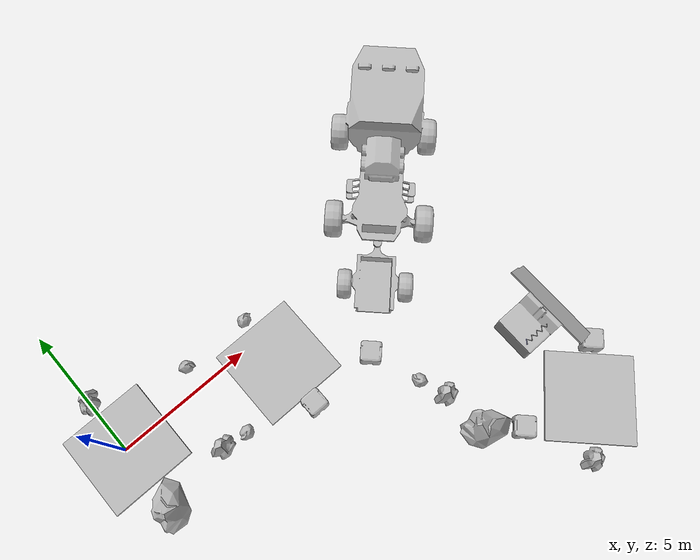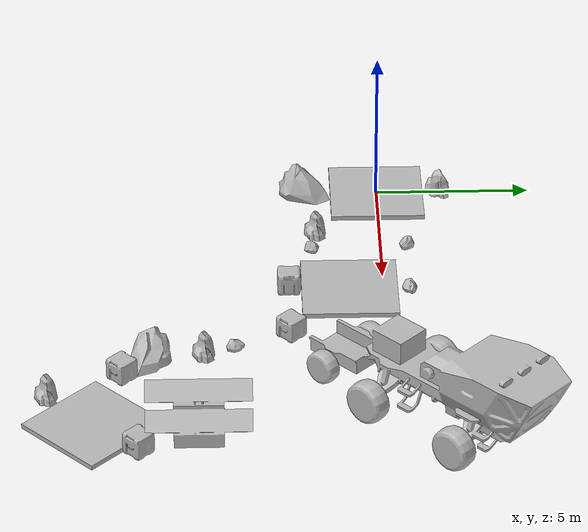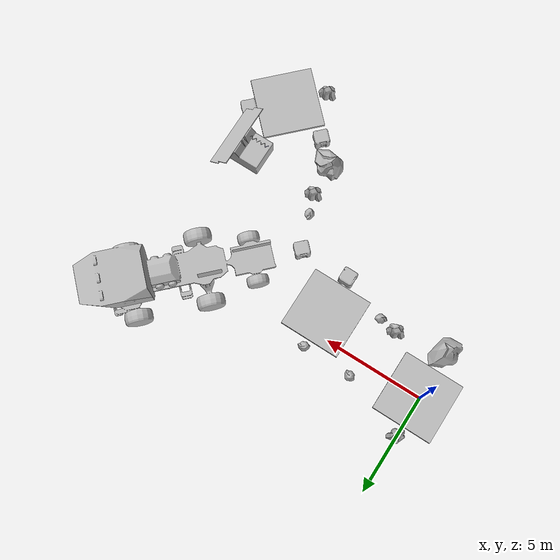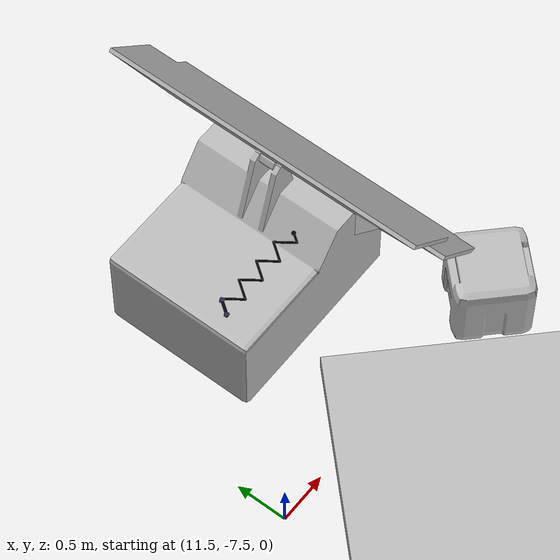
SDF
<sdf version="1.6">
 <world name="SRC_finals">
  <physics type="ode">
   <real_time_update_rate>1000.0</real_time_update_rate>
   <max_step_size>0.001</max_step_size>
   <real_time_factor>1</real_time_factor>
   <ode>
    <solver>
     <type>quick</type>
     <iters>150</iters>
     <precon_iters>0</precon_iters>
     <sor>1.400000</sor>
     <use_dynamic_moi_rescaling>1</use_dynamic_moi_rescaling>
    </solver>
    <constraints>
     <cfm>0.000000</cfm>
     <erp>0.800000</erp>
     <contact_max_correcting_vel>2000.000000</contact_max_correcting_vel>
     <contact_surface_layer>0.01000</contact_surface_layer>
    </constraints>
   </ode>
  </physics>
  <scene>
   <background>0.968627451 0.690196078 0.384313725 1.0</background>
   <grid>0</grid>
   <origin_visual>0</origin_visual>
  </scene>
  <light type="directional" name="sun">
   <pose>0 0 1000 -0.038411929699749825 -1.31937636432259 0</pose>
   <diffuse>0.8 0.8 0.8 1</diffuse>
   <specular>0.2 0.2 0.2 1</specular>
   <attenuation>
    <range>1000</range>
    <constant>0.9</constant>
    <linear>0.01</linear>
    <quadratic>0.001</quadratic>
   </attenuation>
   <direction>-0.5 0.1 -0.9</direction>
  </light>
  <include>
   <name>walkway_1</name>
   <pose>0.09
      0
      -0.052151
      0
      0
      3.141592653589793</pose>
   <uri>model://walkway_finish_opposite</uri>
  </include>
  <include>
   <name>bling_1</name>
   <pose>0.08999999999999968
      -2.624
      0
      0
      0
      3.141592653589793</pose>
   <uri>model://mars_rock_3</uri>
  </include>
  <include>
   <name>bling_2</name>
   <pose>0.0900000000000003
      2.024
      0
      0
      0
      -2.4492935982947064e-16</pose>
   <uri>model://mars_rock_2</uri>
  </include>
  <plugin name="boxT1Start" filename="libBoxContainsPlugin.so">
   <entity>valkyrie</entity>
   <namespace>task1/start</namespace>
   <pose>2.114
        -2.784846821261081e-16
        2.5
        0
        0
        -1.5707963267948968</pose>
   <size>1.524 1 5.0</size>
  </plugin>
  <plugin name="boxT1CP1" filename="libBoxContainsPlugin.so">
   <entity>valkyrie</entity>
   <namespace>task1/checkpoint1</namespace>
   <pose>2.3760000000000003
        0.36199999999999966
        2.5
        0
        0
        1.5707963267948963</pose>
   <size>1 1 5.0</size>
  </plugin>
  <include>
   <name>bling_3</name>
   <pose>3.2532027124746192
      0.8924427124746186
      0
      0
      0
      -0.7853981633974485</pose>
   <uri>model://mars_rock_1</uri>
  </include>
  <include>
   <name>bling_4</name>
   <pose>2.5060414016271593
      -2.0409183542126463
      0
      0
      0
      2.356194490192345</pose>
   <uri>model://mars_rock_2</uri>
  </include>
  <include>
   <name>bling_5</name>
   <pose>3.4539547922204332
      -2.2397649636193724
      0
      0
      0
      3.141592653589793</pose>
   <uri>model://mars_rock_1</uri>
  </include>
  <include>
   <name>walkway_4</name>
   <pose>5.739954792220433
      -1.0777649636193727
      -0.052151
      0
      0
      3.141592653589793</pose>
   <uri>model://walkway_finish_opposite</uri>
  </include>
  <plugin name="boxT1CP4" filename="libBoxContainsPlugin.so">
   <entity>valkyrie</entity>
   <namespace>task1/checkpoint4</namespace>
   <pose>5.739954792220433
        -1.0777649636193727
        2.5
        0
        0
        3.141592653589793</pose>
   <size>3.048 3.048 5.0</size>
  </plugin>
  <include>
   <name>bling_6</name>
   <pose>5.739954792220433
      -3.001764963619373
      0
      0
      0
      3.141592653589793</pose>
   <uri>model://mars_crate</uri>
  </include>
  <include>
   <name>bling_7</name>
   <pose>5.739954792220433
      0.8462350363806274
      0
      0
      0
      -1.8369701987210297e-16</pose>
   <uri>model://mars_rock_1</uri>
  </include>
  <plugin name="boxT2Start" filename="libBoxContainsPlugin.so">
   <entity>valkyrie</entity>
   <namespace>task2/start</namespace>
   <pose>7.763954792220433
        -1.0777649636193727
        2.5
        0
        0
        -1.5707963267948968</pose>
   <size>1.524 1 5.0</size>
  </plugin>
  <include>
   <pose>12.824300042088197
        1.5647454597200912
        0
        0
        0
        2.356194490192345</pose>
   <uri>model://mars_explorer</uri>
  </include>
  <include>
   <name>bling_8</name>
   <pose>8.281846079745815
      -2.97770850262229
      0
      0
      0
      2.356194490192345</pose>
   <uri>model://mars_crate</uri>
  </include>
  <include>
   <name>bling_9</name>
   <pose>9.288900365246533
      -5.650373972961378
      0
      0
      0
      2.356194490192345</pose>
   <uri>model://mars_rock_2</uri>
  </include>
  <include>
   <name>bling_10</name>
   <pose>8.9299408428266
      -4.768781522449238
      0
      0
      0
      1.5707963267948966</pose>
   <uri>model://mars_rock_1</uri>
  </include>
  <include>
   <pose>12.66022813790961
        -5.82485964228697
        0.2
        0
        0
        -1.5707963267948968</pose>
   <uri>model://solar_array</uri>
  </include>
  <model name="solar_panel_cable">
   <self_collide>true</self_collide>
   <pose>13.26022813790961
    -6.224859642286971
    1.05
    0
    0
    3.141592653589793</pose>
   <link name="link_0">
    <inertial><mass>0.05</mass><inertia><ixx>0.0001</ixx><iyy>0.0001</iyy><izz>0.0001</izz></inertia></inertial>
    <visual name="visual">
     <geometry><sphere><radius>0.02</radius></sphere></geometry>
     <material>
      <ambient>0 0 0 1</ambient>
      <emissive>0 0 0 1</emissive>
      <diffuse>0 0 0 1</diffuse>
      <specular>1 1 1 1</specular>
     </material>
    </visual>
   </link>
   <link name="link_1">
    <pose>0.0 0 0 0 1.5707963267948966 0.9424777960769379</pose>
    <inertial>
     <pose>0 0 0.05 0 0 0</pose>
     <mass>0.05</mass>
     <inertia><ixx>0.0001</ixx><iyy>0.0001</iyy><izz>0.0001</izz></inertia>
    </inertial>
    <collision name="cylinder">
     <pose>0 0 0.05 0 0 0</pose>
     <geometry><cylinder><length>0.1</length><radius>0.01</radius></cylinder></geometry>
     <surface>
      <contact><ode><kp>1e5</kp><kd>1</kd><max_vel>0.1</max_vel><min_depth>0.0015</min_depth></ode></contact>
      <friction><ode><mu>1.0</mu><mu2>1.0</mu2></ode></friction>
     </surface>
    </collision>
    <visual name="cylinder">
     <pose>0 0 0.05 0 0 0</pose>
     <geometry><cylinder><length>0.1</length><radius>0.01</radius></cylinder></geometry>
     <material>
      <ambient>0 0 0 1</ambient>
      <emissive>0 0 0 1</emissive>
      <diffuse>0 0 0 1</diffuse>
      <specular>1 1 1 1</specular>
     </material>
    </visual>
    <collision name="sphere">
     <geometry><sphere><radius>0.01</radius></sphere></geometry>
     <surface>
      <contact><ode><kp>1e5</kp><kd>1</kd><max_vel>0.1</max_vel><min_depth>0.0015</min_depth></ode></contact>
      <friction><ode><mu>1.0</mu><mu2>1.0</mu2></ode></friction>
     </surface>
    </collision>
    <visual name="sphere">
     <geometry><sphere><radius>0.01</radius></sphere></geometry>
     <material>
      <ambient>0 0 0 1</ambient>
      <emissive>0 0 0 1</emissive>
      <diffuse>0 0 0 1</diffuse>
      <specular>1 1 1 1</specular>
     </material>
    </visual>
   </link>
   <joint name="joint_1" type="universal">
    <child>link_1</child>
    <parent>link_0</parent>
    <axis>
     <xyz>0 1 0</xyz>
     <limit><lower>-1.5707963267948966</lower><upper>1.5707963267948966</upper></limit>
    </axis>
    <axis2>
     <xyz>-1 0 0</xyz>
     <limit><lower>-1.5707963267948966</lower><upper>1.5707963267948966</upper></limit>
    </axis2>
    <physics><ode><cfm_damping>1</cfm_damping></ode></physics>
   </joint>
   <link name="link_2">
    <pose>0.058778525229247314 0.08090169943749476 0 0 1.5707963267948966 -0.9424777960769379</pose>
    <inertial>
     <pose>0 0 0.05 0 0 0</pose>
     <mass>0.05</mass>
     <inertia><ixx>0.0001</ixx><iyy>0.0001</iyy><izz>0.0001</izz></inertia>
    </inertial>
    <collision name="cylinder">
     <pose>0 0 0.05 0 0 0</pose>
     <geometry><cylinder><length>0.1</length><radius>0.01</radius></cylinder></geometry>
     <surface>
      <contact><ode><kp>1e5</kp><kd>1</kd><max_vel>0.1</max_vel><min_depth>0.0015</min_depth></ode></contact>
      <friction><ode><mu>1.0</mu><mu2>1.0</mu2></ode></friction>
     </surface>
    </collision>
    <visual name="cylinder">
     <pose>0 0 0.05 0 0 0</pose>
     <geometry><cylinder><length>0.1</length><radius>0.01</radius></cylinder></geometry>
     <material>
      <ambient>0 0 0 1</ambient>
      <emissive>0 0 0 1</emissive>
      <diffuse>0 0 0 1</diffuse>
      <specular>1 1 1 1</specular>
     </material>
    </visual>
    <collision name="sphere">
     <geometry><sphere><radius>0.01</radius></sphere></geometry>
     <surface>
      <contact><ode><kp>1e5</kp><kd>1</kd><max_vel>0.1</max_vel><min_depth>0.0015</min_depth></ode></contact>
      <friction><ode><mu>1.0</mu><mu2>1.0</mu2></ode></friction>
     </surface>
    </collision>
    <visual name="sphere">
     <geometry><sphere><radius>0.01</radius></sphere></geometry>
     <material>
      <ambient>0 0 0 1</ambient>
      <emissive>0 0 0 1</emissive>
      <diffuse>0 0 0 1</diffuse>
      <specular>1 1 1 1</specular>
     </material>
    </visual>
   </link>
   <joint name="joint_2" type="universal">
    <child>link_2</child>
    <parent>link_1</parent>
    <axis>
     <xyz>0 1 0</xyz>
     <limit><lower>-1.5707963267948966</lower><upper>1.5707963267948966</upper></limit>
    </axis>
    <axis2>
     <xyz>-1 0 0</xyz>
     <limit><lower>-1.5707963267948966</lower><upper>1.5707963267948966</upper></limit>
    </axis2>
    <physics><ode><cfm_damping>1</cfm_damping></ode></physics>
   </joint>
   <link name="link_3">
    <pose>0.11755705045849463 0 0 0 1.5707963267948966 -0.9424777960769379</pose>
    <inertial>
     <pose>0 0 0.05 0 0 0</pose>
     <mass>0.05</mass>
     <inertia><ixx>0.0001</ixx><iyy>0.0001</iyy><izz>0.0001</izz></inertia>
    </inertial>
    <collision name="cylinder">
     <pose>0 0 0.05 0 0 0</pose>
     <geometry><cylinder><length>0.1</length><radius>0.01</radius></cylinder></geometry>
     <surface>
      <contact><ode><kp>1e5</kp><kd>1</kd><max_vel>0.1</max_vel><min_depth>0.0015</min_depth></ode></contact>
      <friction><ode><mu>1.0</mu><mu2>1.0</mu2></ode></friction>
     </surface>
    </collision>
    <visual name="cylinder">
     <pose>0 0 0.05 0 0 0</pose>
     <geometry><cylinder><length>0.1</length><radius>0.01</radius></cylinder></geometry>
     <material>
      <ambient>0 0 0 1</ambient>
      <emissive>0 0 0 1</emissive>
      <diffuse>0 0 0 1</diffuse>
      <specular>1 1 1 1</specular>
     </material>
    </visual>
    <collision name="sphere">
     <geometry><sphere><radius>0.01</radius></sphere></geometry>
     <surface>
      <contact><ode><kp>1e5</kp><kd>1</kd><max_vel>0.1</max_vel><min_depth>0.0015</min_depth></ode></contact>
      <friction><ode><mu>1.0</mu><mu2>1.0</mu2></ode></friction>
     </surface>
    </collision>
    <visual name="sphere">
     <geometry><sphere><radius>0.01</radius></sphere></geometry>
     <material>
      <ambient>0 0 0 1</ambient>
      <emissive>0 0 0 1</emissive>
      <diffuse>0 0 0 1</diffuse>
      <specular>1 1 1 1</specular>
     </material>
    </visual>
   </link>
   <joint name="joint_3" type="universal">
    <child>link_3</child>
    <parent>link_2</parent>
    <axis>
     <xyz>0 1 0</xyz>
     <limit><lower>-1.5707963267948966</lower><upper>1.5707963267948966</upper></limit>
    </axis>
    <axis2>
     <xyz>-1 0 0</xyz>
     <limit><lower>-1.5707963267948966</lower><upper>1.5707963267948966</upper></limit>
    </axis2>
    <physics><ode><cfm_damping>1</cfm_damping></ode></physics>
   </joint>
   <link name="link_4">
    <pose>0.17633557568774197 -0.08090169943749476 0 0 1.5707963267948966 0.9424777960769379</pose>
    <inertial>
     <pose>0 0 0.05 0 0 0</pose>
     <mass>0.05</mass>
     <inertia><ixx>0.0001</ixx><iyy>0.0001</iyy><izz>0.0001</izz></inertia>
    </inertial>
    <collision name="cylinder">
     <pose>0 0 0.05 0 0 0</pose>
     <geometry><cylinder><length>0.1</length><radius>0.01</radius></cylinder></geometry>
     <surface>
      <contact><ode><kp>1e5</kp><kd>1</kd><max_vel>0.1</max_vel><min_depth>0.0015</min_depth></ode></contact>
      <friction><ode><mu>1.0</mu><mu2>1.0</mu2></ode></friction>
     </surface>
    </collision>
    <visual name="cylinder">
     <pose>0 0 0.05 0 0 0</pose>
     <geometry><cylinder><length>0.1</length><radius>0.01</radius></cylinder></geometry>
     <material>
      <ambient>0 0 0 1</ambient>
      <emissive>0 0 0 1</emissive>
      <diffuse>0 0 0 1</diffuse>
      <specular>1 1 1 1</specular>
     </material>
    </visual>
    <collision name="sphere">
     <geometry><sphere><radius>0.01</radius></sphere></geometry>
     <surface>
      <contact><ode><kp>1e5</kp><kd>1</kd><max_vel>0.1</max_vel><min_depth>0.0015</min_depth></ode></contact>
      <friction><ode><mu>1.0</mu><mu2>1.0</mu2></ode></friction>
     </surface>
    </collision>
    <visual name="sphere">
     <geometry><sphere><radius>0.01</radius></sphere></geometry>
     <material>
      <ambient>0 0 0 1</ambient>
      <emissive>0 0 0 1</emissive>
      <diffuse>0 0 0 1</diffuse>
      <specular>1 1 1 1</specular>
     </material>
    </visual>
   </link>
   <joint name="joint_4" type="universal">
    <child>link_4</child>
    <parent>link_3</parent>
    <axis>
     <xyz>0 1 0</xyz>
     <limit><lower>-1.5707963267948966</lower><upper>1.5707963267948966</upper></limit>
    </axis>
    <axis2>
     <xyz>-1 0 0</xyz>
     <limit><lower>-1.5707963267948966</lower><upper>1.5707963267948966</upper></limit>
    </axis2>
    <physics><ode><cfm_damping>1</cfm_damping></ode></physics>
   </joint>
   <link name="link_5">
    <pose>0.23511410091698925 0 0 0 1.5707963267948966 0.9424777960769379</pose>
    <inertial>
     <pose>0 0 0.05 0 0 0</pose>
     <mass>0.05</mass>
     <inertia><ixx>0.0001</ixx><iyy>0.0001</iyy><izz>0.0001</izz></inertia>
    </inertial>
    <collision name="cylinder">
     <pose>0 0 0.05 0 0 0</pose>
     <geometry><cylinder><length>0.1</length><radius>0.01</radius></cylinder></geometry>
     <surface>
      <contact><ode><kp>1e5</kp><kd>1</kd><max_vel>0.1</max_vel><min_depth>0.0015</min_depth></ode></contact>
      <friction><ode><mu>1.0</mu><mu2>1.0</mu2></ode></friction>
     </surface>
    </collision>
    <visual name="cylinder">
     <pose>0 0 0.05 0 0 0</pose>
     <geometry><cylinder><length>0.1</length><radius>0.01</radius></cylinder></geometry>
     <material>
      <ambient>0 0 0 1</ambient>
      <emissive>0 0 0 1</emissive>
      <diffuse>0 0 0 1</diffuse>
      <specular>1 1 1 1</specular>
     </material>
    </visual>
    <collision name="sphere">
     <geometry><sphere><radius>0.01</radius></sphere></geometry>
     <surface>
      <contact><ode><kp>1e5</kp><kd>1</kd><max_vel>0.1</max_vel><min_depth>0.0015</min_depth></ode></contact>
      <friction><ode><mu>1.0</mu><mu2>1.0</mu2></ode></friction>
     </surface>
    </collision>
    <visual name="sphere">
     <geometry><sphere><radius>0.01</radius></sphere></geometry>
     <material>
      <ambient>0 0 0 1</ambient>
      <emissive>0 0 0 1</emissive>
      <diffuse>0 0 0 1</diffuse>
      <specular>1 1 1 1</specular>
     </material>
    </visual>
   </link>
   <joint name="joint_5" type="universal">
    <child>link_5</child>
    <parent>link_4</parent>
    <axis>
     <xyz>0 1 0</xyz>
     <limit><lower>-1.5707963267948966</lower><upper>1.5707963267948966</upper></limit>
    </axis>
    <axis2>
     <xyz>-1 0 0</xyz>
     <limit><lower>-1.5707963267948966</lower><upper>1.5707963267948966</upper></limit>
    </axis2>
    <physics><ode><cfm_damping>1</cfm_damping></ode></physics>
   </joint>
   <link name="link_6">
    <pose>0.29389262614623657 0.08090169943749476 0 0 1.5707963267948966 -0.9424777960769379</pose>
    <inertial>
     <pose>0 0 0.05 0 0 0</pose>
     <mass>0.05</mass>
     <inertia><ixx>0.0001</ixx><iyy>0.0001</iyy><izz>0.0001</izz></inertia>
    </inertial>
    <collision name="cylinder">
     <pose>0 0 0.05 0 0 0</pose>
     <geometry><cylinder><length>0.1</length><radius>0.01</radius></cylinder></geometry>
     <surface>
      <contact><ode><kp>1e5</kp><kd>1</kd><max_vel>0.1</max_vel><min_depth>0.0015</min_depth></ode></contact>
      <friction><ode><mu>1.0</mu><mu2>1.0</mu2></ode></friction>
     </surface>
    </collision>
    <visual name="cylinder">
     <pose>0 0 0.05 0 0 0</pose>
     <geometry><cylinder><length>0.1</length><radius>0.01</radius></cylinder></geometry>
     <material>
      <ambient>0 0 0 1</ambient>
      <emissive>0 0 0 1</emissive>
      <diffuse>0 0 0 1</diffuse>
      <specular>1 1 1 1</specular>
     </material>
    </visual>
    <collision name="sphere">
     <geometry><sphere><radius>0.01</radius></sphere></geometry>
     <surface>
      <contact><ode><kp>1e5</kp><kd>1</kd><max_vel>0.1</max_vel><min_depth>0.0015</min_depth></ode></contact>
      <friction><ode><mu>1.0</mu><mu2>1.0</mu2></ode></friction>
     </surface>
    </collision>
    <visual name="sphere">
     <geometry><sphere><radius>0.01</radius></sphere></geometry>
     <material>
      <ambient>0 0 0 1</ambient>
      <emissive>0 0 0 1</emissive>
      <diffuse>0 0 0 1</diffuse>
      <specular>1 1 1 1</specular>
     </material>
    </visual>
   </link>
   <joint name="joint_6" type="universal">
    <child>link_6</child>
    <parent>link_5</parent>
    <axis>
     <xyz>0 1 0</xyz>
     <limit><lower>-1.5707963267948966</lower><upper>1.5707963267948966</upper></limit>
    </axis>
    <axis2>
     <xyz>-1 0 0</xyz>
     <limit><lower>-1.5707963267948966</lower><upper>1.5707963267948966</upper></limit>
    </axis2>
    <physics><ode><cfm_damping>1</cfm_damping></ode></physics>
   </joint>
   <link name="link_7">
    <pose>0.35267115137548394 0 0 0 1.5707963267948966 -0.9424777960769379</pose>
    <inertial>
     <pose>0 0 0.05 0 0 0</pose>
     <mass>0.05</mass>
     <inertia><ixx>0.0001</ixx><iyy>0.0001</iyy><izz>0.0001</izz></inertia>
    </inertial>
    <collision name="cylinder">
     <pose>0 0 0.05 0 0 0</pose>
     <geometry><cylinder><length>0.1</length><radius>0.01</radius></cylinder></geometry>
     <surface>
      <contact><ode><kp>1e5</kp><kd>1</kd><max_vel>0.1</max_vel><min_depth>0.0015</min_depth></ode></contact>
      <friction><ode><mu>1.0</mu><mu2>1.0</mu2></ode></friction>
     </surface>
    </collision>
    <visual name="cylinder">
     <pose>0 0 0.05 0 0 0</pose>
     <geometry><cylinder><length>0.1</length><radius>0.01</radius></cylinder></geometry>
     <material>
      <ambient>0 0 0 1</ambient>
      <emissive>0 0 0 1</emissive>
      <diffuse>0 0 0 1</diffuse>
      <specular>1 1 1 1</specular>
     </material>
    </visual>
    <collision name="sphere">
     <geometry><sphere><radius>0.01</radius></sphere></geometry>
     <surface>
      <contact><ode><kp>1e5</kp><kd>1</kd><max_vel>0.1</max_vel><min_depth>0.0015</min_depth></ode></contact>
      <friction><ode><mu>1.0</mu><mu2>1.0</mu2></ode></friction>
     </surface>
    </collision>
    <visual name="sphere">
     <geometry><sphere><radius>0.01</radius></sphere></geometry>
     <material>
      <ambient>0 0 0 1</ambient>
      <emissive>0 0 0 1</emissive>
      <diffuse>0 0 0 1</diffuse>
      <specular>1 1 1 1</specular>
     </material>
    </visual>
   </link>
   <joint name="joint_7" type="universal">
    <child>link_7</child>
    <parent>link_6</parent>
    <axis>
     <xyz>0 1 0</xyz>
     <limit><lower>-1.5707963267948966</lower><upper>1.5707963267948966</upper></limit>
    </axis>
    <axis2>
     <xyz>-1 0 0</xyz>
     <limit><lower>-1.5707963267948966</lower><upper>1.5707963267948966</upper></limit>
    </axis2>
    <physics><ode><cfm_damping>1</cfm_damping></ode></physics>
   </joint>
   <link name="link_8">
    <pose>0.41144967660473125 -0.08090169943749476 0 0 1.5707963267948966 0.9424777960769379</pose>
    <inertial>
     <pose>0 0 0.05 0 0 0</pose>
     <mass>0.05</mass>
     <inertia><ixx>0.0001</ixx><iyy>0.0001</iyy><izz>0.0001</izz></inertia>
    </inertial>
    <collision name="cylinder">
     <pose>0 0 0.05 0 0 0</pose>
     <geometry><cylinder><length>0.1</length><radius>0.01</radius></cylinder></geometry>
     <surface>
      <contact><ode><kp>1e5</kp><kd>1</kd><max_vel>0.1</max_vel><min_depth>0.0015</min_depth></ode></contact>
      <friction><ode><mu>1.0</mu><mu2>1.0</mu2></ode></friction>
     </surface>
    </collision>
    <visual name="cylinder">
     <pose>0 0 0.05 0 0 0</pose>
     <geometry><cylinder><length>0.1</length><radius>0.01</radius></cylinder></geometry>
     <material>
      <ambient>0 0 0 1</ambient>
      <emissive>0 0 0 1</emissive>
      <diffuse>0 0 0 1</diffuse>
      <specular>1 1 1 1</specular>
     </material>
    </visual>
    <collision name="sphere">
     <geometry><sphere><radius>0.01</radius></sphere></geometry>
     <surface>
      <contact><ode><kp>1e5</kp><kd>1</kd><max_vel>0.1</max_vel><min_depth>0.0015</min_depth></ode></contact>
      <friction><ode><mu>1.0</mu><mu2>1.0</mu2></ode></friction>
     </surface>
    </collision>
    <visual name="sphere">
     <geometry><sphere><radius>0.01</radius></sphere></geometry>
     <material>
      <ambient>0 0 0 1</ambient>
      <emissive>0 0 0 1</emissive>
      <diffuse>0 0 0 1</diffuse>
      <specular>1 1 1 1</specular>
     </material>
    </visual>
   </link>
   <joint name="joint_8" type="universal">
    <child>link_8</child>
    <parent>link_7</parent>
    <axis>
     <xyz>0 1 0</xyz>
     <limit><lower>-1.5707963267948966</lower><upper>1.5707963267948966</upper></limit>
    </axis>
    <axis2>
     <xyz>-1 0 0</xyz>
     <limit><lower>-1.5707963267948966</lower><upper>1.5707963267948966</upper></limit>
    </axis2>
    <physics><ode><cfm_damping>1</cfm_damping></ode></physics>
   </joint>
   <link name="link_9">
    <pose>0.4702282018339785 0 0 0 1.5707963267948966 0.9424777960769379</pose>
    <inertial>
     <pose>0 0 0.05 0 0 0</pose>
     <mass>0.05</mass>
     <inertia><ixx>0.0001</ixx><iyy>0.0001</iyy><izz>0.0001</izz></inertia>
    </inertial>
    <collision name="cylinder">
     <pose>0 0 0.05 0 0 0</pose>
     <geometry><cylinder><length>0.1</length><radius>0.01</radius></cylinder></geometry>
     <surface>
      <contact><ode><kp>1e5</kp><kd>1</kd><max_vel>0.1</max_vel><min_depth>0.0015</min_depth></ode></contact>
      <friction><ode><mu>1.0</mu><mu2>1.0</mu2></ode></friction>
     </surface>
    </collision>
    <visual name="cylinder">
     <pose>0 0 0.05 0 0 0</pose>
     <geometry><cylinder><length>0.1</length><radius>0.01</radius></cylinder></geometry>
     <material>
      <ambient>0 0 0 1</ambient>
      <emissive>0 0 0 1</emissive>
      <diffuse>0 0 0 1</diffuse>
      <specular>1 1 1 1</specular>
     </material>
    </visual>
    <collision name="sphere">
     <geometry><sphere><radius>0.01</radius></sphere></geometry>
     <surface>
      <contact><ode><kp>1e5</kp><kd>1</kd><max_vel>0.1</max_vel><min_depth>0.0015</min_depth></ode></contact>
      <friction><ode><mu>1.0</mu><mu2>1.0</mu2></ode></friction>
     </surface>
    </collision>
    <visual name="sphere">
     <geometry><sphere><radius>0.01</radius></sphere></geometry>
     <material>
      <ambient>0 0 0 1</ambient>
      <emissive>0 0 0 1</emissive>
      <diffuse>0 0 0 1</diffuse>
      <specular>1 1 1 1</specular>
     </material>
    </visual>
   </link>
   <joint name="joint_9" type="universal">
    <child>link_9</child>
    <parent>link_8</parent>
    <axis>
     <xyz>0 1 0</xyz>
     <limit><lower>-1.5707963267948966</lower><upper>1.5707963267948966</upper></limit>
    </axis>
    <axis2>
     <xyz>-1 0 0</xyz>
     <limit><lower>-1.5707963267948966</lower><upper>1.5707963267948966</upper></limit>
    </axis2>
    <physics><ode><cfm_damping>1</cfm_damping></ode></physics>
   </joint>
   <link name="link_10">
    <pose>0.5290067270632258 0.08090169943749476 0 0 1.5707963267948966 -0.9424777960769379</pose>
    <inertial>
     <pose>0 0 0.05 0 0 0</pose>
     <mass>0.05</mass>
     <inertia><ixx>0.0001</ixx><iyy>0.0001</iyy><izz>0.0001</izz></inertia>
    </inertial>
    <collision name="cylinder">
     <pose>0 0 0.05 0 0 0</pose>
     <geometry><cylinder><length>0.1</length><radius>0.01</radius></cylinder></geometry>
     <surface>
      <contact><ode><kp>1e5</kp><kd>1</kd><max_vel>0.1</max_vel><min_depth>0.0015</min_depth></ode></contact>
      <friction><ode><mu>1.0</mu><mu2>1.0</mu2></ode></friction>
     </surface>
    </collision>
    <visual name="cylinder">
     <pose>0 0 0.05 0 0 0</pose>
     <geometry><cylinder><length>0.1</length><radius>0.01</radius></cylinder></geometry>
     <material>
      <ambient>0 0 0 1</ambient>
      <emissive>0 0 0 1</emissive>
      <diffuse>0 0 0 1</diffuse>
      <specular>1 1 1 1</specular>
     </material>
    </visual>
    <collision name="sphere">
     <geometry><sphere><radius>0.01</radius></sphere></geometry>
     <surface>
      <contact><ode><kp>1e5</kp><kd>1</kd><max_vel>0.1</max_vel><min_depth>0.0015</min_depth></ode></contact>
      <friction><ode><mu>1.0</mu><mu2>1.0</mu2></ode></friction>
     </surface>
    </collision>
    <visual name="sphere">
     <geometry><sphere><radius>0.01</radius></sphere></geometry>
     <material>
      <ambient>0 0 0 1</ambient>
      <emissive>0 0 0 1</emissive>
      <diffuse>0 0 0 1</diffuse>
      <specular>1 1 1 1</specular>
     </material>
    </visual>
   </link>
   <joint name="joint_10" type="universal">
    <child>link_10</child>
    <parent>link_9</parent>
    <axis>
     <xyz>0 1 0</xyz>
     <limit><lower>-1.5707963267948966</lower><upper>1.5707963267948966</upper></limit>
    </axis>
    <axis2>
     <xyz>-1 0 0</xyz>
     <limit><lower>-1.5707963267948966</lower><upper>1.5707963267948966</upper></limit>
    </axis2>
    <physics><ode><cfm_damping>1</cfm_damping></ode></physics>
   </joint>
   <link name="link_11">
    <pose>0.5877852522924731 0 0 0 1.5707963267948966 -0.9424777960769379</pose>
    <inertial>
     <pose>0 0 0.05 0 0 0</pose>
     <mass>0.05</mass>
     <inertia><ixx>0.0001</ixx><iyy>0.0001</iyy><izz>0.0001</izz></inertia>
    </inertial>
    <collision name="cylinder">
     <pose>0 0 0.05 0 0 0</pose>
     <geometry><cylinder><length>0.1</length><radius>0.01</radius></cylinder></geometry>
     <surface>
      <contact><ode><kp>1e5</kp><kd>1</kd><max_vel>0.1</max_vel><min_depth>0.0015</min_depth></ode></contact>
      <friction><ode><mu>1.0</mu><mu2>1.0</mu2></ode></friction>
     </surface>
    </collision>
    <visual name="cylinder">
     <pose>0 0 0.05 0 0 0</pose>
     <geometry><cylinder><length>0.1</length><radius>0.01</radius></cylinder></geometry>
     <material>
      <ambient>0 0 0 1</ambient>
      <emissive>0 0 0 1</emissive>
      <diffuse>0 0 0 1</diffuse>
      <specular>1 1 1 1</specular>
     </material>
    </visual>
    <collision name="sphere">
     <geometry><sphere><radius>0.01</radius></sphere></geometry>
     <surface>
      <contact><ode><kp>1e5</kp><kd>1</kd><max_vel>0.1</max_vel><min_depth>0.0015</min_depth></ode></contact>
      <friction><ode><mu>1.0</mu><mu2>1.0</mu2></ode></friction>
     </surface>
    </collision>
    <visual name="sphere">
     <geometry><sphere><radius>0.01</radius></sphere></geometry>
     <material>
      <ambient>0 0 0 1</ambient>
      <emissive>0 0 0 1</emissive>
      <diffuse>0 0 0 1</diffuse>
      <specular>1 1 1 1</specular>
     </material>
    </visual>
   </link>
   <joint name="joint_11" type="universal">
    <child>link_11</child>
    <parent>link_10</parent>
    <axis>
     <xyz>0 1 0</xyz>
     <limit><lower>-1.5707963267948966</lower><upper>1.5707963267948966</upper></limit>
    </axis>
    <axis2>
     <xyz>-1 0 0</xyz>
     <limit><lower>-1.5707963267948966</lower><upper>1.5707963267948966</upper></limit>
    </axis2>
    <physics><ode><cfm_damping>1</cfm_damping></ode></physics>
   </joint>
   <link name="link_12">
    <pose>0.6465637775217205 -0.08090169943749476 0 0 1.5707963267948966 0.9424777960769379</pose>
    <inertial>
     <pose>0 0 0.05 0 0 0</pose>
     <mass>0.05</mass>
     <inertia><ixx>0.0001</ixx><iyy>0.0001</iyy><izz>0.0001</izz></inertia>
    </inertial>
    <collision name="cylinder">
     <pose>0 0 0.05 0 0 0</pose>
     <geometry><cylinder><length>0.1</length><radius>0.01</radius></cylinder></geometry>
     <surface>
      <contact><ode><kp>1e5</kp><kd>1</kd><max_vel>0.1</max_vel><min_depth>0.0015</min_depth></ode></contact>
      <friction><ode><mu>1.0</mu><mu2>1.0</mu2></ode></friction>
     </surface>
    </collision>
    <visual name="cylinder">
     <pose>0 0 0.05 0 0 0</pose>
     <geometry><cylinder><length>0.1</length><radius>0.01</radius></cylinder></geometry>
     <material>
      <ambient>0 0 0 1</ambient>
      <emissive>0 0 0 1</emissive>
      <diffuse>0 0 0 1</diffuse>
      <specular>1 1 1 1</specular>
     </material>
    </visual>
    <collision name="sphere">
     <geometry><sphere><radius>0.01</radius></sphere></geometry>
     <surface>
      <contact><ode><kp>1e5</kp><kd>1</kd><max_vel>0.1</max_vel><min_depth>0.0015</min_depth></ode></contact>
      <friction><ode><mu>1.0</mu><mu2>1.0</mu2></ode></friction>
     </surface>
    </collision>
    <visual name="sphere">
     <geometry><sphere><radius>0.01</radius></sphere></geometry>
     <material>
      <ambient>0 0 0 1</ambient>
      <emissive>0 0 0 1</emissive>
      <diffuse>0 0 0 1</diffuse>
      <specular>1 1 1 1</specular>
     </material>
    </visual>
   </link>
   <joint name="joint_12" type="universal">
    <child>link_12</child>
    <parent>link_11</parent>
    <axis>
     <xyz>0 1 0</xyz>
     <limit><lower>-1.5707963267948966</lower><upper>1.5707963267948966</upper></limit>
    </axis>
    <axis2>
     <xyz>-1 0 0</xyz>
     <limit><lower>-1.5707963267948966</lower><upper>1.5707963267948966</upper></limit>
    </axis2>
    <physics><ode><cfm_damping>1</cfm_damping></ode></physics>
   </joint>
   <link name="link_13">
    <pose>0.7053423027509679 0 0 0 1.5707963267948966 0.9424777960769379</pose>
    <inertial>
     <pose>0 0 0.05 0 0 0</pose>
     <mass>0.05</mass>
     <inertia><ixx>0.0001</ixx><iyy>0.0001</iyy><izz>0.0001</izz></inertia>
    </inertial>
    <collision name="cylinder">
     <pose>0 0 0.05 0 0 0</pose>
     <geometry><cylinder><length>0.1</length><radius>0.01</radius></cylinder></geometry>
     <surface>
      <contact><ode><kp>1e5</kp><kd>1</kd><max_vel>0.1</max_vel><min_depth>0.0015</min_depth></ode></contact>
      <friction><ode><mu>1.0</mu><mu2>1.0</mu2></ode></friction>
     </surface>
    </collision>
    <visual name="cylinder">
     <pose>0 0 0.05 0 0 0</pose>
     <geometry><cylinder><length>0.1</length><radius>0.01</radius></cylinder></geometry>
     <material>
      <ambient>0 0 0 1</ambient>
      <emissive>0 0 0 1</emissive>
      <diffuse>0 0 0 1</diffuse>
      <specular>1 1 1 1</specular>
     </material>
    </visual>
    <collision name="sphere">
     <geometry><sphere><radius>0.01</radius></sphere></geometry>
     <surface>
      <contact><ode><kp>1e5</kp><kd>1</kd><max_vel>0.1</max_vel><min_depth>0.0015</min_depth></ode></contact>
      <friction><ode><mu>1.0</mu><mu2>1.0</mu2></ode></friction>
     </surface>
    </collision>
    <visual name="sphere">
     <geometry><sphere><radius>0.01</radius></sphere></geometry>
     <material>
      <ambient>0 0 0 1</ambient>
      <emissive>0 0 0 1</emissive>
      <diffuse>0 0 0 1</diffuse>
      <specular>1 1 1 1</specular>
     </material>
    </visual>
   </link>
   <joint name="joint_13" type="universal">
    <child>link_13</child>
    <parent>link_12</parent>
    <axis>
     <xyz>0 1 0</xyz>
     <limit><lower>-1.5707963267948966</lower><upper>1.5707963267948966</upper></limit>
    </axis>
    <axis2>
     <xyz>-1 0 0</xyz>
     <limit><lower>-1.5707963267948966</lower><upper>1.5707963267948966</upper></limit>
    </axis2>
    <physics><ode><cfm_damping>1</cfm_damping></ode></physics>
   </joint>
   <link name="link_14">
    <pose>0.7641208279802151 0.08090169943749476 0 0 1.5707963267948966 -0.9424777960769379</pose>
    <inertial>
     <pose>0 0 0.05 0 0 0</pose>
     <mass>0.05</mass>
     <inertia><ixx>0.0001</ixx><iyy>0.0001</iyy><izz>0.0001</izz></inertia>
    </inertial>
    <collision name="cylinder">
     <pose>0 0 0.05 0 0 0</pose>
     <geometry><cylinder><length>0.1</length><radius>0.01</radius></cylinder></geometry>
     <surface>
      <contact><ode><kp>1e5</kp><kd>1</kd><max_vel>0.1</max_vel><min_depth>0.0015</min_depth></ode></contact>
      <friction><ode><mu>1.0</mu><mu2>1.0</mu2></ode></friction>
     </surface>
    </collision>
    <visual name="cylinder">
     <pose>0 0 0.05 0 0 0</pose>
     <geometry><cylinder><length>0.1</length><radius>0.01</radius></cylinder></geometry>
     <material>
      <ambient>0 0 0 1</ambient>
      <emissive>0 0 0 1</emissive>
      <diffuse>0 0 0 1</diffuse>
      <specular>1 1 1 1</specular>
     </material>
    </visual>
    <collision name="sphere">
     <geometry><sphere><radius>0.01</radius></sphere></geometry>
     <surface>
      <contact><ode><kp>1e5</kp><kd>1</kd><max_vel>0.1</max_vel><min_depth>0.0015</min_depth></ode></contact>
      <friction><ode><mu>1.0</mu><mu2>1.0</mu2></ode></friction>
     </surface>
    </collision>
    <visual name="sphere">
     <geometry><sphere><radius>0.01</radius></sphere></geometry>
     <material>
      <ambient>0 0 0 1</ambient>
      <emissive>0 0 0 1</emissive>
      <diffuse>0 0 0 1</diffuse>
      <specular>1 1 1 1</specular>
     </material>
    </visual>
   </link>
   <joint name="joint_14" type="universal">
    <child>link_14</child>
    <parent>link_13</parent>
    <axis>
     <xyz>0 1 0</xyz>
     <limit><lower>-1.5707963267948966</lower><upper>1.5707963267948966</upper></limit>
    </axis>
    <axis2>
     <xyz>-1 0 0</xyz>
     <limit><lower>-1.5707963267948966</lower><upper>1.5707963267948966</upper></limit>
    </axis2>
    <physics><ode><cfm_damping>1</cfm_damping></ode></physics>
   </joint>
   <link name="link_15">
    <pose>0.8228993532094625 0 0 0 1.5707963267948966 -0.9424777960769379</pose>
    <inertial>
     <pose>0 0 0.05 0 0 0</pose>
     <mass>0.05</mass>
     <inertia><ixx>0.0001</ixx><iyy>0.0001</iyy><izz>0.0001</izz></inertia>
    </inertial>
    <collision name="cylinder">
     <pose>0 0 0.05 0 0 0</pose>
     <geometry><cylinder><length>0.1</length><radius>0.01</radius></cylinder></geometry>
     <surface>
      <contact><ode><kp>1e5</kp><kd>1</kd><max_vel>0.1</max_vel><min_depth>0.0015</min_depth></ode></contact>
      <friction><ode><mu>1.0</mu><mu2>1.0</mu2></ode></friction>
     </surface>
    </collision>
    <visual name="cylinder">
     <pose>0 0 0.05 0 0 0</pose>
     <geometry><cylinder><length>0.1</length><radius>0.01</radius></cylinder></geometry>
     <material>
      <ambient>0 0 0 1</ambient>
      <emissive>0 0 0 1</emissive>
      <diffuse>0 0 0 1</diffuse>
      <specular>1 1 1 1</specular>
     </material>
    </visual>
    <collision name="sphere">
     <geometry><sphere><radius>0.01</radius></sphere></geometry>
     <surface>
      <contact><ode><kp>1e5</kp><kd>1</kd><max_vel>0.1</max_vel><min_depth>0.0015</min_depth></ode></contact>
      <friction><ode><mu>1.0</mu><mu2>1.0</mu2></ode></friction>
     </surface>
    </collision>
    <visual name="sphere">
     <geometry><sphere><radius>0.01</radius></sphere></geometry>
     <material>
      <ambient>0 0 0 1</ambient>
      <emissive>0 0 0 1</emissive>
      <diffuse>0 0 0 1</diffuse>
      <specular>1 1 1 1</specular>
     </material>
    </visual>
   </link>
   <joint name="joint_15" type="universal">
    <child>link_15</child>
    <parent>link_14</parent>
    <axis>
     <xyz>0 1 0</xyz>
     <limit><lower>-1.5707963267948966</lower><upper>1.5707963267948966</upper></limit>
    </axis>
    <axis2>
     <xyz>-1 0 0</xyz>
     <limit><lower>-1.5707963267948966</lower><upper>1.5707963267948966</upper></limit>
    </axis2>
    <physics><ode><cfm_damping>1</cfm_damping></ode></physics>
   </joint>
   <link name="link_16">
    <pose>0.8816778784387097 -0.08090169943749476 0 0 1.5707963267948966 0.9424777960769379</pose>
    <inertial>
     <pose>0 0 0.05 0 0 0</pose>
     <mass>0.05</mass>
     <inertia><ixx>0.0001</ixx><iyy>0.0001</iyy><izz>0.0001</izz></inertia>
    </inertial>
    <collision name="cylinder">
     <pose>0 0 0.09000000000000001 0 0 0</pose>
     <geometry>
      <cylinder><length>0.18000000000000002</length><radius>0.013999999999999999</radius></cylinder>
     </geometry>
     <surface>
      <contact><ode><kp>1e5</kp><kd>1</kd><max_vel>0.1</max_vel><min_depth>0.0015</min_depth></ode></contact>
      <friction><ode><mu>1.0</mu><mu2>1.0</mu2></ode></friction>
     </surface>
    </collision>
    <visual name="cylinder">
     <pose>0 0 0.09000000000000001 0 0 0</pose>
     <geometry>
      <cylinder><length>0.18000000000000002</length><radius>0.013999999999999999</radius></cylinder>
     </geometry>
     <material>
      <ambient>0 0 0.3 1</ambient>
      <emissive>0 0 0 1</emissive>
      <diffuse>0 0 0.1 1</diffuse>
      <specular>1 1 1 1</specular>
     </material>
    </visual>
    <collision name="sphere">
     <geometry><sphere><radius>0.013999999999999999</radius></sphere></geometry>
     <surface>
      <contact><ode><kp>1e5</kp><kd>1</kd><max_vel>0.1</max_vel><min_depth>0.0015</min_depth></ode></contact>
      <friction><ode><mu>1.0</mu><mu2>1.0</mu2></ode></friction>
     </surface>
    </collision>
    <visual name="sphere">
     <geometry><sphere><radius>0.013999999999999999</radius></sphere></geometry>
     <material>
      <ambient>0 0 0.3 1</ambient>
      <emissive>0 0 0 1</emissive>
      <diffuse>0 0 0.1 1</diffuse>
      <specular>1 1 1 1</specular>
     </material>
    </visual>
    <collision name="plug_outer_1">
     <pose>0 0 0.16200000000000003 0 0 0</pose>
     <geometry><cylinder><length>0.010000000000000002</length><radius>0.025</radius></cylinder></geometry>
     <surface>
      <contact><ode><kp>1e5</kp><kd>1</kd><max_vel>0.1</max_vel><min_depth>0.0015</min_depth></ode></contact>
      <friction><ode><mu>1.0</mu><mu2>1.0</mu2></ode></friction>
     </surface>
    </collision>
    <visual name="plug_outer_1">
     <pose>0 0 0.16200000000000003 0 0 0</pose>
     <geometry><cylinder><length>0.010000000000000002</length><radius>0.025</radius></cylinder></geometry>
     <material>
      <ambient>0 0 0.3 1</ambient>
      <emissive>0 0 0.5 1</emissive>
      <diffuse>0 0 0.1 1</diffuse>
      <specular>1 1 1 1</specular>
     </material>
    </visual>
    <collision name="plug_middle_1">
     <pose>0 0 0.16200000000000003 0 0 0</pose>
     <geometry><cylinder><length>0.020000000000000004</length><radius>0.017</radius></cylinder></geometry>
     <surface>
      <contact><ode><kp>1e5</kp><kd>1</kd><max_vel>0.1</max_vel><min_depth>0.0015</min_depth></ode></contact>
      <friction><ode><mu>1.0</mu><mu2>1.0</mu2></ode></friction>
     </surface>
    </collision>
    <visual name="plug_middle_1">
     <pose>0 0 0.16200000000000003 0 0 0</pose>
     <geometry><cylinder><length>0.020000000000000004</length><radius>0.017</radius></cylinder></geometry>
     <material>
      <ambient>0 0 0.7 1</ambient>
      <emissive>0 0 0 1</emissive>
      <diffuse>0 0 0.1 1</diffuse>
      <specular>1 1 1 1</specular>
     </material>
    </visual>
    <collision name="plug_outer_2">
     <pose>0 0 0.018000000000000002 0 0 0</pose>
     <geometry><cylinder><length>0.010000000000000002</length><radius>0.025</radius></cylinder></geometry>
     <surface>
      <contact><ode><kp>1e5</kp><kd>1</kd><max_vel>0.1</max_vel><min_depth>0.0015</min_depth></ode></contact>
      <friction><ode><mu>1.0</mu><mu2>1.0</mu2></ode></friction>
     </surface>
    </collision>
    <visual name="plug_outer_2">
     <pose>0 0 0.018000000000000002 0 0 0</pose>
     <geometry><cylinder><length>0.010000000000000002</length><radius>0.025</radius></cylinder></geometry>
     <material>
      <ambient>0 0 0.3 1</ambient>
      <emissive>0 0 0.5 1</emissive>
      <diffuse>0 0 0.1 1</diffuse>
      <specular>1 1 1 1</specular>
     </material>
    </visual>
    <collision name="plug_middle_2">
     <pose>0 0 0.018000000000000002 0 0 0</pose>
     <geometry><cylinder><length>0.020000000000000004</length><radius>0.017</radius></cylinder></geometry>
     <surface>
      <contact><ode><kp>1e5</kp><kd>1</kd><max_vel>0.1</max_vel><min_depth>0.0015</min_depth></ode></contact>
      <friction><ode><mu>1.0</mu><mu2>1.0</mu2></ode></friction>
     </surface>
    </collision>
    <visual name="plug_middle_2">
     <pose>0 0 0.018000000000000002 0 0 0</pose>
     <geometry><cylinder><length>0.020000000000000004</length><radius>0.017</radius></cylinder></geometry>
     <material>
      <ambient>0 0 0.7 1</ambient>
      <emissive>0 0 0 1</emissive>
      <diffuse>0 0 0.1 1</diffuse>
      <specular>1 1 1 1</specular>
     </material>
    </visual>
    <sensor name="tip_sensor" type="contact">
     <contact>
      <collision>plug_outer_1</collision>
      <collision>plug_outer_2</collision>
      <collision>plug_middle_1</collision>
      <collision>plug_middle_2</collision>
      <collision>cylinder</collision>
      <collision>sphere</collision>
     </contact>
    </sensor>
   </link>
   <joint name="joint_16" type="universal">
    <child>link_16</child>
    <parent>link_15</parent>
    <axis>
     <xyz>0 1 0</xyz>
     <limit><lower>-1.5707963267948966</lower><upper>1.5707963267948966</upper></limit>
    </axis>
    <axis2>
     <xyz>-1 0 0</xyz>
     <limit><lower>-1.5707963267948966</lower><upper>1.5707963267948966</upper></limit>
    </axis2>
    <physics><ode><cfm_damping>1</cfm_damping></ode></physics>
   </joint>
   <joint name="world" type="fixed"><child>link_0</child><parent>world</parent></joint>
   <plugin name="touch_valkyrie_cable" filename="libTouchPlugin.so">
    <sensor>tip_sensor</sensor>
    <target>valkyrie</target>
    <time>0.5</time>
    <namespace>task2/checkpoint4</namespace>
   </plugin>
  </model>
  <plugin name="boxT2CP2" filename="libBoxContainsPlugin.so">
   <entity>solar_panel</entity>
   <namespace>task2/checkpoint2</namespace>
   <pose>12.66022813790961
        -5.82485964228697
        1.1
        0
        0
        -1.5707963267948968</pose>
   <size>1.47 0.95 0.45</size>
  </plugin>
  <include>
   <name>bling_11</name>
   <pose>9.307705806445973
      -7.3707363146696725
      0
      0
      0
      1.5707963267948966</pose>
   <uri>model://mars_rock_3</uri>
  </include>
  <include>
   <name>bling_12</name>
   <pose>10.437376006984561
      -8.181618087063157
      0
      0
      0
      2.356194490192345</pose>
   <uri>model://mars_crate</uri>
  </include>
  <include>
   <name>walkway_11</name>
   <pose>12.875480188515777
      -8.976406109116837
      -0.052151
      0
      0
      2.356194490192345</pose>
   <uri>model://walkway_finish_opposite</uri>
  </include>
  <plugin name="boxT2CP6" filename="libBoxContainsPlugin.so">
   <entity>valkyrie</entity>
   <namespace>task2/checkpoint6</namespace>
   <pose>12.875480188515777
        -8.976406109116837
        2.5
        0
        0
        2.356194490192345</pose>
   <size>3.048 3.048 5.0</size>
  </plugin>
  <include>
   <name>bling_13</name>
   <pose>11.444296063394205
      -10.407590234238409
      0
      0
      0
      2.356194490192345</pose>
   <uri>model://mars_rock_2</uri>
  </include>
  <include>
   <name>bling_14</name>
   <pose>14.235953635518694
      -7.615932662113919
      0
      0
      0
      -0.7853981633974485</pose>
   <uri>model://mars_crate</uri>
  </include>
  <plugin name="boxT3Start" filename="libBoxContainsPlugin.so">
   <entity>valkyrie</entity>
   <namespace>task3/start</namespace>
   <pose>14.306664313637349
        -10.407590234238409
        2.5
        0
        0
        -2.356194490192345</pose>
   <size>1.524 1 5.0</size>
  </plugin>
  <plugin name="boxT3CP1" filename="libBoxContainsPlugin.so">
   <entity>valkyrie</entity>
   <namespace>task3/checkpoint1</namespace>
   <pose>17.83340579466345
        -12.13725763586557
        2.92
        0
        0
        -1.2246467991473532e-16</pose>
   <size>1.0 2.50 2.44</size>
  </plugin>
  <plugin name="boxT3CP3" filename="libBoxContainsPlugin.so">
   <entity>valkyrie</entity>
   <namespace>task3/checkpoint3</namespace>
   <pose>20.97320579466345
        -14.31725763586557
        2.81
        0
        0
        -1.5707963267948968</pose>
   <size>1.00 1.55 2.88</size>
  </plugin>
  <plugin name="boxT3CP8" filename="libBoxContainsPlugin.so">
   <entity>valkyrie</entity>
   <namespace>task3/checkpoint8</namespace>
   <pose>20.95340579466345
        -27.81725763586557
        2.68
        0
        0
        -1.5707963267948968</pose>
   <size>1.5 1.5 5.0</size>
  </plugin>
  <plugin name="finals" filename="libFinalsPlugin.so">
   <task1>
    <timeout>1800</timeout>
    <checkpoint1>
     <skip_robot_pose>2.3760000000000003
              0.36199999999999966
              1.257
              0
              0
              1.5707963267948963</skip_robot_pose>
    </checkpoint1>
    <checkpoint2>
     <skip_robot_pose>2.3760000000000003
              0.36199999999999966
              1.257
              0
              0
              1.5707963267948963</skip_robot_pose>
    </checkpoint2>
    <checkpoint4>
     <skip_robot_pose>5.739954792220433
              -1.0777649636193725
              1.257
              0
              0
              -1.8369701987210297e-16</skip_robot_pose>
    </checkpoint4>
   </task1>
   <task2>
    <timeout>3600</timeout>
    <checkpoint1>
     <start_robot_pose>5.739954792220433
              -1.0777649636193725
              1.257
              0
              0
              -1.8369701987210297e-16</start_robot_pose>
     <skip_robot_pose>5.739954792220433
              -1.0777649636193725
              1.257
              0
              0
              -1.8369701987210297e-16</skip_robot_pose>
    </checkpoint1>
    <checkpoint2>
     <skip_robot_pose>11.460228137909612
              -5.82485964228697
              1.257
              0
              0
              -2.83276944882399e-16</skip_robot_pose>
     <panel_pose>12.529986971210649
              -5.443056197348945
              0.8999999999999999
              0
              0
              2.726160829490021</panel_pose>
    </checkpoint2>
    <checkpoint3>
     <skip_robot_pose>11.460228137909612
              -5.82485964228697
              1.257
              0
              0
              -2.83276944882399e-16</skip_robot_pose>
    </checkpoint3>
    <checkpoint4>
     <skip_robot_pose>11.460228137909612
              -5.82485964228697
              1.257
              0
              0
              -2.83276944882399e-16</skip_robot_pose>
    </checkpoint4>
    <checkpoint5>
     <skip_robot_pose>11.460228137909612
              -5.82485964228697
              1.257
              0
              0
              -2.83276944882399e-16</skip_robot_pose>
    </checkpoint5>
    <checkpoint6>
     <skip_robot_pose>12.875480188515777
              -8.976406109116837
              1.257
              0
              0
              -0.7853981633974484</skip_robot_pose>
    </checkpoint6>
   </task2>
   <task3>
    <timeout>7200</timeout>
    <checkpoint1>
     <start_robot_pose>12.875480188515777
              -8.976406109116837
              1.257
              0
              0
              -0.7853981633974484</start_robot_pose>
     <skip_robot_pose>17.83340579466345
              -12.13725763586557
              2.957
              0
              0
              -1.2246467991473532e-16</skip_robot_pose>
    </checkpoint1>
    <checkpoint2>
     <skip_robot_pose>17.83340579466345
              -12.13725763586557
              2.957
              0
              0
              -1.2246467991473532e-16</skip_robot_pose>
    </checkpoint2>
    <checkpoint3>
     <insert_entity>
      <light name="habitat_lamp" type="spot">
       <pose>21.19140579466345
                  -13.65725763586557
                  4.2
                  -1.462
                  0
                  -1.2246467991473532e-16</pose>
       <diffuse>1 1 1 1</diffuse>
       <specular>0.1 0.1 0.1 1</specular>
       <attenuation>
        <range>10</range>
        <constant>0.5</constant>
        <linear>0.01</linear>
        <quadratic>0.001</quadratic>
       </attenuation>
       <cast_shadows>0</cast_shadows>
       <direction>0 0 -1</direction>
       <spot><inner_angle>0.6</inner_angle><outer_angle>3.141592653589793</outer_angle><falloff>0.5</falloff></spot>
      </light>
     </insert_entity>
     <insert_entity>
      <include>
       <pose>21.92505780179912
                    -18.945561480357153
                    2.0
                    0
                    0
                    -1.4212962001299052</pose>
       <uri>model://space_table</uri>
      </include>
     </insert_entity>
     <insert_entity>
      <model name="air_leak_detector">
       <pose>22.12617013018131
    -18.553580786286187
    2.79448
    0
    0
    0.9071761334047099</pose>
       <link name="base">
        <inertial>
         <pose>0
      -0.00063
      0
      0
      0
      0</pose>
         <inertia>
          <ixx>0.0006035883333333333</ixx>
          <iyy>0.003206729933333333</iyy>
          <izz>0.003333989666666666</izz>
         </inertia>
         <mass>1.0</mass>
        </inertial>
        <collision name="collision">
         <pose>0 0 -0.022000000000000002 0 0 -1.5707963267948966</pose>
         <geometry>
          <mesh><scale>0.02 0.02 0.02</scale><uri>model://air_leak_detector/meshes/air_leak_detector.obj</uri></mesh>
         </geometry>
         <surface>
          <contact><ode><kp>1e5</kp><kd>1</kd><max_vel>0.1</max_vel><min_depth>0.0015</min_depth></ode></contact>
         </surface>
        </collision>
        <visual name="visual">
         <pose>0 0 -0.022000000000000002 0 0 -1.5707963267948966</pose>
         <geometry>
          <mesh><scale>0.02 0.02 0.02</scale><uri>model://air_leak_detector/meshes/air_leak_detector.obj</uri></mesh>
         </geometry>
        </visual>
        <sensor name="logical_camera" type="logical_camera">
         <logical_camera>
          <near>0.2</near>
          <far>0.5</far>
          <horizontal_fov>0.3490658503988659</horizontal_fov>
          <aspect_ratio>1</aspect_ratio>
         </logical_camera>
         <visualize>true</visualize>
         <always_on>true</always_on>
         <update_rate>10</update_rate>
        </sensor>
        <sensor name="contact_sensor" type="contact"><contact><collision>collision</collision></contact></sensor>
       </link>
       <plugin name="touch_valkyrie_detector" filename="libTouchPlugin.so">
        <sensor>contact_sensor</sensor>
        <target>valkyrie</target>
        <time>0.5</time>
        <namespace>task3/checkpoint4</namespace>
       </plugin>
      </model>
     </insert_entity>
     <insert_entity>
      <include>
       <pose>22.16997615329728
                    -19.313297330755578
                    2.8000000000000003
                    0
                    0
                    -0.5081161941465538</pose>
       <uri>model://leak_patch_tool</uri>
      </include>
     </insert_entity>
     <insert_entity>
      <model name="leak">
       <static>true</static>
       <pose>25.037302381188255 -15.884638896568699 3.6065050836189485 0 0 0</pose>
       <link name="base">
        <collision name="collision">
         <geometry><sphere><radius>0.02</radius></sphere></geometry>
         <surface><contact><collide_bitmask>0x10000</collide_bitmask></contact></surface>
        </collision>
        <sensor name="leak_sensor" type="contact"><contact><collision>collision</collision></contact></sensor>
       </link>
      </model>
     </insert_entity>
     <insert_entity>
      <include>
       <name>mars_crate_15</name>
       <pose>24.47930196475958
      -20.294488769512135
      1.8
      0
      0
      -2.1649135265151096</pose>
       <uri>model://mars_crate</uri>
      </include>
     </insert_entity>
     <insert_entity>
      <include>
       <name>mars_crate_16</name>
       <pose>24.47930196475958
      -20.294488769512135
      2.5
      0
      0
      -2.1483374948561127</pose>
       <uri>model://mars_crate</uri>
      </include>
     </insert_entity>
     <insert_entity>
      <include>
       <name>mars_crate_long_17</name>
       <pose>21.461428197276526
      -22.658150391710777
      1.8
      0
      0
      2.4265569191299248</pose>
       <uri>model://mars_crate_long</uri>
      </include>
     </insert_entity>
     <insert_entity>
      <include>
       <name>mars_crate_long_18</name>
       <pose>21.461428197276526
      -22.658150391710777
      2.5
      0
      0
      2.6745490905501166</pose>
       <uri>model://mars_crate_long</uri>
      </include>
     </insert_entity>
     <insert_entity>
      <include>
       <name>mars_crate_long_19</name>
       <pose>18.892810156721552
      -21.958067611038786
      1.8
      0
      0
      1.3121272719386805</pose>
       <uri>model://mars_crate_long</uri>
      </include>
     </insert_entity>
     <insert_entity>
      <include>
       <name>mars_crate_long_20</name>
       <pose>18.892810156721552
      -21.958067611038786
      2.5
      0
      0
      1.5296048154707855</pose>
       <uri>model://mars_crate_long</uri>
      </include>
     </insert_entity>
     <insert_entity>
      <include>
       <name>mars_crate_long_21</name>
       <pose>18.892810156721552
      -21.958067611038786
      3.2
      0
      0
      1.5829586901427053</pose>
       <uri>model://mars_crate_long</uri>
      </include>
     </insert_entity>
     <insert_entity>
      <include>
       <name>mars_crate_long_22</name>
       <pose>17.762331919005828
      -18.416868970869906
      1.8
      0
      0
      -2.316915860718021</pose>
       <uri>model://mars_crate_long</uri>
      </include>
     </insert_entity>
     <insert_entity>
      <include>
       <name>mars_crate_23</name>
       <pose>19.034152719960733
      -16.233304828244236
      1.8
      0
      0
      1.3486756959319917</pose>
       <uri>model://mars_crate</uri>
      </include>
     </insert_entity>
     <insert_entity>
      <include>
       <name>mars_crate_long_24</name>
       <pose>21.29196179878337
      -15.802926618305303
      1.8
      0
      0
      -2.53362651077867</pose>
       <uri>model://mars_crate_long</uri>
      </include>
     </insert_entity>
     <insert_entity>
      <include>
       <name>mars_crate_long_25</name>
       <pose>21.29196179878337
      -15.802926618305303
      2.5
      0
      0
      -1.9692323179957483</pose>
       <uri>model://mars_crate_long</uri>
      </include>
     </insert_entity>
     <insert_entity>
      <include>
       <name>mars_crate_long_26</name>
       <pose>21.29196179878337
      -15.802926618305303
      3.2
      0
      0
      -1.3838547843410192</pose>
       <uri>model://mars_crate_long</uri>
      </include>
     </insert_entity>
     <insert_entity>
      <include>
       <name>mars_crate_27</name>
       <pose>24.16624706718863
      -16.771901434209546
      1.8
      0
      0
      0.7007595193465128</pose>
       <uri>model://mars_crate</uri>
      </include>
     </insert_entity>
     <skip_robot_pose>20.97320579466345
              -14.31725763586557
              2.957
              0
              0
              -1.5707963267948968</skip_robot_pose>
    </checkpoint3>
    <checkpoint4>
     <delete_entity>satellite_dish</delete_entity>
     <delete_entity>solar_panel</delete_entity>
     <delete_entity>solar_panel_cable</delete_entity>
     <delete_entity>solar_array</delete_entity>
     <delete_entity>mars_explorer</delete_entity>
     <delete_entity>walkway_1</delete_entity>
     <delete_entity>walkway_2</delete_entity>
     <delete_entity>walkway_3</delete_entity>
     <delete_entity>walkway_4</delete_entity>
     <delete_entity>walkway_5</delete_entity>
     <delete_entity>walkway_6</delete_entity>
     <delete_entity>walkway_7</delete_entity>
     <delete_entity>walkway_8</delete_entity>
     <delete_entity>walkway_9</delete_entity>
     <delete_entity>walkway_10</delete_entity>
     <delete_entity>walkway_11</delete_entity>
     <delete_entity>walkway_12</delete_entity>
     <delete_entity>walkway_13</delete_entity>
     <delete_entity>bling_1</delete_entity>
     <delete_entity>bling_2</delete_entity>
     <delete_entity>bling_3</delete_entity>
     <delete_entity>bling_4</delete_entity>
     <delete_entity>bling_5</delete_entity>
     <delete_entity>bling_6</delete_entity>
     <delete_entity>bling_7</delete_entity>
     <delete_entity>bling_8</delete_entity>
     <delete_entity>bling_9</delete_entity>
     <delete_entity>bling_10</delete_entity>
     <delete_entity>bling_11</delete_entity>
     <delete_entity>bling_12</delete_entity>
     <delete_entity>bling_13</delete_entity>
     <delete_entity>bling_14</delete_entity>
     <skip_robot_pose>20.97320579466345
              -14.31725763586557
              2.957
              0
              0
              -1.5707963267948968</skip_robot_pose>
    </checkpoint4>
    <checkpoint5>
     <skip_robot_pose>20.97320579466345
              -14.31725763586557
              2.957
              0
              0
              -1.5707963267948968</skip_robot_pose>
    </checkpoint5>
    <checkpoint6>
     <skip_robot_pose>20.97320579466345
              -14.31725763586557
              2.957
              0
              0
              -1.5707963267948968</skip_robot_pose>
    </checkpoint6>
    <checkpoint7>
     <skip_robot_pose>20.97320579466345
              -14.31725763586557
              2.957
              0
              0
              -1.5707963267948968</skip_robot_pose>
    </checkpoint7>
    <checkpoint8>
     <skip_robot_pose>20.95340579466345
              -27.81725763586557
              2.957
              0
              0
              -1.5707963267948968</skip_robot_pose>
    </checkpoint8>
   </task3>
  </plugin>
 </world>
</sdf>

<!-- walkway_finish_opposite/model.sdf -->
<sdf version="1.5">
  <model name="walkway_finish_opposite">
    <static>true</static>
    <link name="link">
      <collision name="collision">
        <pose>0 0 0.076075 0 0 0</pose>
        <geometry>
          <box>
            <size>3.048 3.048 0.15215</size>
          </box>
        </geometry>
      </collision>

      <visual name="visual">
        <geometry>
          <mesh>
            <scale>0.001 0.001 0.001</scale>
            <uri>model://walkway_finish_opposite/meshes/walkway_finish_opposite.obj</uri>
          </mesh>
        </geometry>
      </visual>
    </link>
  </model>
</sdf>

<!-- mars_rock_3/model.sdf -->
<sdf version="1.5">
  <model name="mars_rock_3">
    <static>true</static>
    <link name="link">
      <collision name="collision">
        <geometry>
          <mesh>
            <uri>model://mars_rock_3/meshes/mars_rock_3.obj</uri>
            <scale>0.03 0.03 0.03</scale>
          </mesh>
        </geometry>
      </collision>
      <visual name="visual">
        <geometry>
          <mesh>
            <uri>model://mars_rock_3/meshes/mars_rock_3.obj</uri>
            <scale>0.03 0.03 0.03</scale>
          </mesh>
        </geometry>
      </visual>
    </link>
  </model>
</sdf>

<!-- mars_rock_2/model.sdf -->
<sdf version="1.5">
  <model name="mars_rock_2">
    <static>true</static>
    <link name="link">
      <collision name="collision">
        <geometry>
          <mesh>
            <uri>model://mars_rock_2/meshes/mars_rock_2.obj</uri>
            <scale>0.03 0.03 0.03</scale>
          </mesh>
        </geometry>
      </collision>
      <visual name="visual">
        <geometry>
          <mesh>
            <uri>model://mars_rock_2/meshes/mars_rock_2.obj</uri>
            <scale>0.03 0.03 0.03</scale>
          </mesh>
        </geometry>
      </visual>
    </link>
  </model>
</sdf>

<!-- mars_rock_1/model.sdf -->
<sdf version="1.5">
  <model name="mars_rock_1">
    <static>true</static>
    <link name="link">
      <collision name="collision">
        <geometry>
          <mesh>
            <uri>model://mars_rock_1/meshes/mars_rock_1.obj</uri>
            <scale>0.03 0.03 0.03</scale>
          </mesh>
        </geometry>
      </collision>
      <visual name="visual">
        <geometry>
          <mesh>
            <uri>model://mars_rock_1/meshes/mars_rock_1.obj</uri>
            <scale>0.03 0.03 0.03</scale>
          </mesh>
        </geometry>
      </visual>
    </link>
  </model>
</sdf>

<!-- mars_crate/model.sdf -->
<sdf version="1.5">
  <model name="mars_crate">
    <static>true</static>
    <link name="link">
      <collision name="collision">
        <pose>0 0 0.36 0 0 0</pose>
        <geometry>
          <box>
            <size>0.72 0.72 0.72</size>
          </box>
        </geometry>
      </collision>
      <visual name="visual">
        <geometry>
          <mesh>
            <uri>model://mars_crate/meshes/crate.obj</uri>
            <scale>0.03 0.03 0.03</scale>
          </mesh>
        </geometry>
      </visual>
    </link>
  </model>
</sdf>

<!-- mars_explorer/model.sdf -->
<sdf version="1.6">
  <model name="mars_explorer">
    <static>1</static>
    <link name="link">

      <visual name="visual">
        <geometry>
          <mesh>
            <uri>model://mars_explorer/meshes/mars_explorer.obj</uri>
            <scale>0.0254 0.0254 0.0254</scale>
          </mesh>
        </geometry>
      </visual>

      <collision name="trailer_left">
        <pose>0.5728 4.0715 0.696 0 0 0</pose>
        <geometry>
          <box>
            <size>0.057 1.905 0.51</size>
          </box>
        </geometry>
        <surface>
          <contact>
            <ode>
              <kp>1e5</kp>
              <kd>1</kd>
              <max_vel>0.1</max_vel>
              <min_depth>0.0015</min_depth>
            </ode>
          </contact>
        </surface>
      </collision>

      <collision name="trailer_left_top">
        <pose>0.6065 4.0715 0.9142 0 0 0</pose>
        <geometry>
          <box>
            <size>0.125 1.905 0.074</size>
          </box>
        </geometry>
        <surface>
          <contact>
            <ode>
              <kp>1e5</kp>
              <kd>1</kd>
              <max_vel>0.1</max_vel>
              <min_depth>0.0015</min_depth>
            </ode>
          </contact>
        </surface>
      </collision>

      <collision name="trailer_left_handle">
        <pose>0.67495 4.069 0.9142 0 0 0</pose>
        <geometry>
          <box>
            <size>0.220321 0.375 0.074</size>
          </box>
        </geometry>
        <surface>
          <contact>
            <ode>
              <kp>1e5</kp>
              <kd>1</kd>
              <max_vel>0.1</max_vel>
              <min_depth>0.0015</min_depth>
            </ode>
          </contact>
        </surface>
      </collision>

      <collision name="trailer_left_handle_edge_1">
        <pose>0.6783 3.828 0.9142 0 0 -0.681263</pose>
        <geometry>
          <box>
            <size>0.1 0.2155 0.074</size>
          </box>
        </geometry>
        <surface>
          <contact>
            <ode>
              <kp>1e5</kp>
              <kd>1</kd>
              <max_vel>0.1</max_vel>
              <min_depth>0.0015</min_depth>
            </ode>
          </contact>
        </surface>
      </collision>

      <collision name="trailer_left_handle_edge_2">
        <pose>0.6783 4.309 0.9142 0 0 0.681263</pose>
        <geometry>
          <box>
            <size>0.1 0.2155 0.074</size>
          </box>
        </geometry>
        <surface>
          <contact>
            <ode>
              <kp>1e5</kp>
              <kd>1</kd>
              <max_vel>0.1</max_vel>
              <min_depth>0.0015</min_depth>
            </ode>
          </contact>
        </surface>
      </collision>

      <collision name="trailer_right">
        <pose>-0.5728 4.075 0.696 0 0 0</pose>
        <geometry>
          <box>
            <size>0.057 1.915 0.51</size>
          </box>
        </geometry>
        <surface>
          <contact>
            <ode>
              <kp>1e5</kp>
              <kd>1</kd>
              <max_vel>0.1</max_vel>
              <min_depth>0.0015</min_depth>
            </ode>
          </contact>
        </surface>
      </collision>

      <collision name="trailer_right_top">
        <pose>-0.6065 4.0715 0.9142 0 0 0</pose>
        <geometry>
          <box>
            <size>0.125 1.905 0.074</size>
          </box>
        </geometry>
        <surface>
          <contact>
            <ode>
              <kp>1e5</kp>
              <kd>1</kd>
              <max_vel>0.1</max_vel>
              <min_depth>0.0015</min_depth>
            </ode>
          </contact>
        </surface>
      </collision>

      <collision name="trailer_right_handle">
        <pose>-0.67495 4.069 0.9142 0 0 0</pose>
        <geometry>
          <box>
            <size>0.220321 0.375 0.074</size>
          </box>
        </geometry>
        <surface>
          <contact>
            <ode>
              <kp>1e5</kp>
              <kd>1</kd>
              <max_vel>0.1</max_vel>
              <min_depth>0.0015</min_depth>
            </ode>
          </contact>
        </surface>
      </collision>

      <collision name="trailer_right_handle_edge_1">
        <pose>-0.6783 3.828 0.9142 0 0 0.681263</pose>
        <geometry>
          <box>
            <size>0.1 0.2155 0.074</size>
          </box>
        </geometry>
        <surface>
          <contact>
            <ode>
              <kp>1e5</kp>
              <kd>1</kd>
              <max_vel>0.1</max_vel>
              <min_depth>0.0015</min_depth>
            </ode>
          </contact>
        </surface>
      </collision>

      <collision name="trailer_right_handle_edge_2">
        <pose>-0.6783 4.309 0.9142 0 0 -0.681263</pose>
        <geometry>
          <box>
            <size>0.1 0.2155 0.074</size>
          </box>
        </geometry>
        <surface>
          <contact>
            <ode>
              <kp>1e5</kp>
              <kd>1</kd>
              <max_vel>0.1</max_vel>
              <min_depth>0.0015</min_depth>
            </ode>
          </contact>
        </surface>
      </collision>

      <collision name="trailer_bottom">
        <pose>0 4.0715 0.4755 0 0 0</pose>
        <geometry>
          <box>
            <size>1.16 1.905 0.065</size>
          </box>
        </geometry>
        <surface>
          <contact>
            <ode>
              <kp>1e6</kp>
              <kd>1</kd>
              <max_vel>0.1</max_vel>
              <min_depth>0.0015</min_depth>
            </ode>
          </contact>
        </surface>
      </collision>

      <collision name="trailer_back">
        <pose>0 3.1505 0.696 0 0 0</pose>
        <geometry>
          <box>
            <size>1.160 0.066 0.51</size>
          </box>
        </geometry>
        <surface>
          <contact>
            <ode>
              <kp>1e5</kp>
              <kd>1</kd>
              <max_vel>0.1</max_vel>
              <min_depth>0.0015</min_depth>
            </ode>
          </contact>
        </surface>
      </collision>

      <collision name="wheel_right_back">
        <pose>-1.0586 4.07 0.505 0 -1.5707 0</pose>
        <geometry>
          <cylinder>
            <radius>0.54</radius>
            <length>0.49</length>
          </cylinder>
        </geometry>
        <surface>
          <contact>
            <ode>
              <kp>1e5</kp>
              <kd>1</kd>
              <max_vel>0.1</max_vel>
              <min_depth>0.0015</min_depth>
            </ode>
          </contact>
        </surface>
      </collision>

      <collision name="wheel_left_back">
        <pose>1.0586 4.07 0.505 0 -1.5707 0</pose>
        <geometry>
          <cylinder>
            <radius>0.54</radius>
            <length>0.49</length>
          </cylinder>
        </geometry>
        <surface>
          <contact>
            <ode>
              <kp>1e5</kp>
              <kd>1</kd>
              <max_vel>0.1</max_vel>
              <min_depth>0.0015</min_depth>
            </ode>
          </contact>
        </surface>
      </collision>

      <collision name="wheel_right_center">
        <pose>-1.6 1.735 0.64 0 -1.5707 0</pose>
        <geometry>
          <cylinder>
            <radius>0.67</radius>
            <length>0.63</length>
          </cylinder>
        </geometry>
        <surface>
          <contact>
            <ode>
              <kp>1e5</kp>
              <kd>1</kd>
              <max_vel>0.1</max_vel>
              <min_depth>0.0015</min_depth>
            </ode>
          </contact>
        </surface>
      </collision>

      <collision name="wheel_left_center">
        <pose>1.6 1.735 0.64 0 -1.5707 0</pose>
        <geometry>
          <cylinder>
            <radius>0.67</radius>
            <length>0.63</length>
          </cylinder>
        </geometry>
        <surface>
          <contact>
            <ode>
              <kp>1e5</kp>
              <kd>1</kd>
              <max_vel>0.1</max_vel>
              <min_depth>0.0015</min_depth>
            </ode>
          </contact>
        </surface>
      </collision>

      <collision name="wheel_right_front">
        <pose>-1.6 -1.678 0.64 0 -1.5707 0</pose>
        <geometry>
          <cylinder>
            <radius>0.67</radius>
            <length>0.63</length>
          </cylinder>
        </geometry>
        <surface>
          <contact>
            <ode>
              <kp>1e5</kp>
              <kd>1</kd>
              <max_vel>0.1</max_vel>
              <min_depth>0.0015</min_depth>
            </ode>
          </contact>
        </surface>
      </collision>

      <collision name="wheel_left_front">
        <pose>1.6 -1.678 0.64 0 -1.5707 0</pose>
        <geometry>
          <cylinder>
            <radius>0.67</radius>
            <length>0.63</length>
          </cylinder>
        </geometry>
        <surface>
          <contact>
            <ode>
              <kp>1e5</kp>
              <kd>1</kd>
              <max_vel>0.1</max_vel>
              <min_depth>0.0015</min_depth>
            </ode>
          </contact>
        </surface>
      </collision>

      <collision name="chassis">
        <pose>0 -0.562963 2.020171 0 0 0</pose>
        <geometry>
          <box>
            <size>2.332756 6.825834 2.262449</size>
          </box>
        </geometry>
        <surface>
          <contact>
            <ode>
              <kp>1e5</kp>
              <kd>1</kd>
              <max_vel>0.1</max_vel>
              <min_depth>0.0015</min_depth>
            </ode>
          </contact>
        </surface>
      </collision>

    </link>
  </model>
</sdf>

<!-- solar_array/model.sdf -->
<sdf version="1.6">

  <model name="solar_array">

    <static>true</static>

    <link name="link">

      <visual name="visual">
        <geometry>
          <mesh>
            <uri>model://solar_array/meshes/solar_array.obj</uri>
            <scale>0.0254 0.0254 0.0254</scale>
          </mesh>
        </geometry>
      </visual>

      <collision name="collision">
        <geometry>
          <mesh>
            <uri>model://solar_array/meshes/solar_array.obj</uri>
            <scale>0.0252 0.0252 0.0252</scale>
          </mesh>
        </geometry>
      </collision>

      <collision name="collision_contact">
        <pose>0 0 0.25 0 0 0</pose>
        <geometry>
          <box>
            <size>1.498 0.99 0.897</size>
          </box>
        </geometry>
        <surface>
          <contact>
            <ode>
              <kp>1e6</kp>
              <kd>1</kd>
              <max_vel>0.1</max_vel>
              <min_depth>0.0015</min_depth>
            </ode>
          </contact>
        </surface>
      </collision>

    </link>

  </model>

</sdf>
